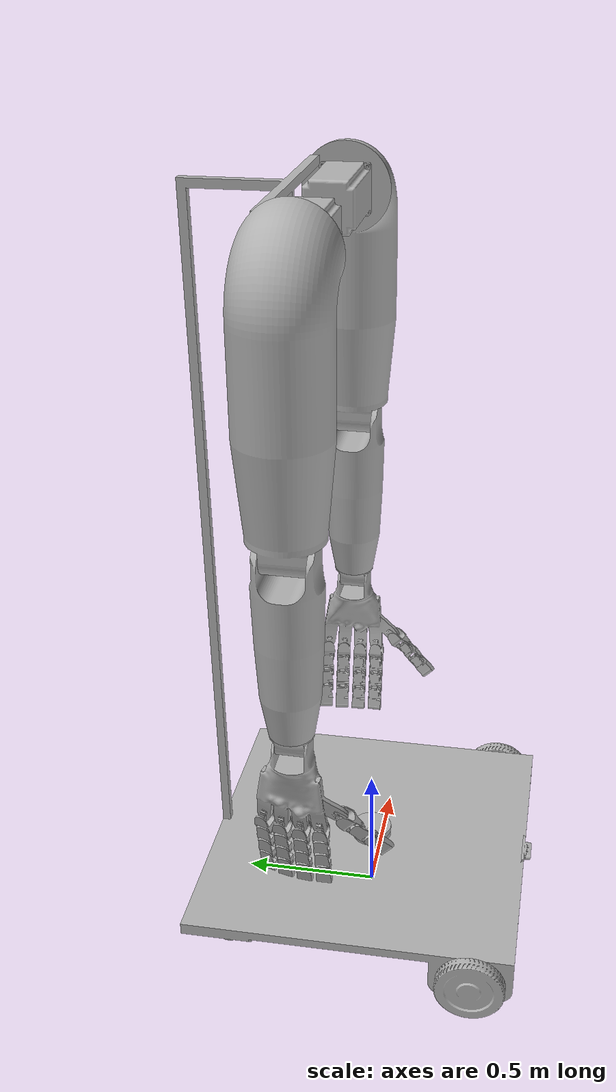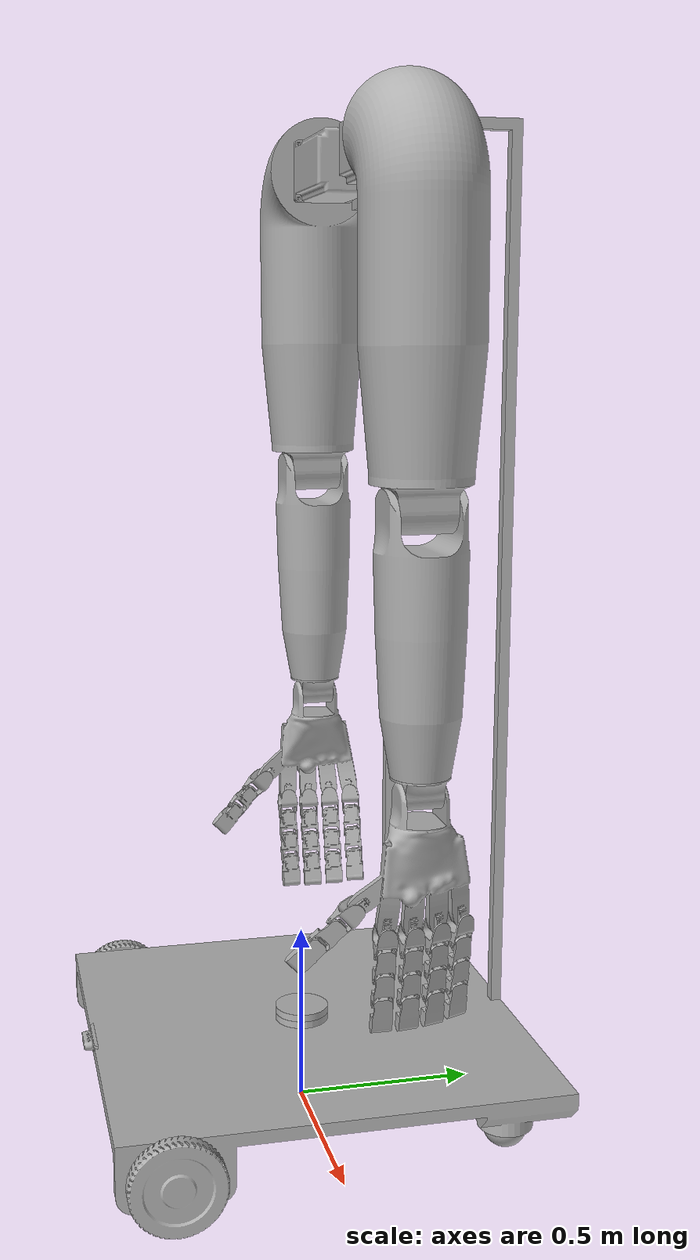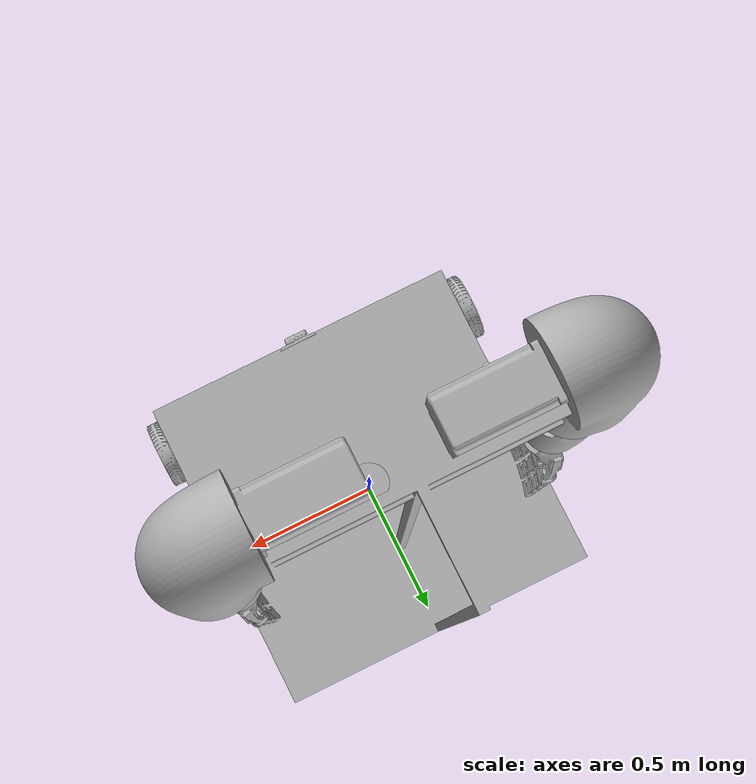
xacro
<?xml version="1.0" ?>
<robot name="hproject" xmlns:xacro="http://www.ros.org/wiki/xacro">

<xacro:include filename="$(find hproject_description)/urdf/materials.xacro" />
<xacro:include filename="$(find hproject_description)/urdf/hproject.trans" />
<xacro:include filename="$(find hproject_description)/urdf/hproject.gazebo" />
<link name="base_link">
  <inertial>
    <origin xyz="-3.1442865304222692e-15 0.26145061991792107 0.40081245927985315" rpy="0 0 0"/>
    <mass value="372.0085391721659"/>
    <inertia ixx="185.554019" iyy="184.647479" izz="91.735258" ixy="-0.0" iyz="-7.399111" ixz="-0.0"/>
  </inertial>
  <visual>
    <origin xyz="0 0 0" rpy="0 0 0"/>
    <geometry>
      <mesh filename="package://hproject_description/meshes/base_link.stl" scale="0.001 0.001 0.001"/>
    </geometry>
    <material name="silver"/>
  </visual>
  <collision>
    <origin xyz="0 0 0" rpy="0 0 0"/>
    <geometry>
      <mesh filename="package://hproject_description/meshes/base_link.stl" scale="0.001 0.001 0.001"/>
    </geometry>
  </collision>
</link>

<link name="pinky_lateral_link_R_1">
  <inertial>
    <origin xyz="0.025162658632176704 -0.006289922186428376 -0.018941953802106837" rpy="0 0 0"/>
    <mass value="0.3479532548461513"/>
    <inertia ixx="0.000218" iyy="0.000264" izz="0.000228" ixy="1.6e-05" iyz="3e-06" ixz="-1.3e-05"/>
  </inertial>
  <visual>
    <origin xyz="0.562592 -0.287941 -0.730502" rpy="0 0 0"/>
    <geometry>
      <mesh filename="package://hproject_description/meshes/pinky_lateral_link_R_1.stl" scale="0.001 0.001 0.001"/>
    </geometry>
    <material name="silver"/>
  </visual>
  <collision>
    <origin xyz="0.562592 -0.287941 -0.730502" rpy="0 0 0"/>
    <geometry>
      <mesh filename="package://hproject_description/meshes/pinky_lateral_link_R_1.stl" scale="0.001 0.001 0.001"/>
    </geometry>
  </collision>
</link>

<link name="pinky_proximal_link_R_1">
  <inertial>
    <origin xyz="0.00814301783439042 0.02563595324629586 -0.01601587517939662" rpy="0 0 0"/>
    <mass value="0.5045183303050147"/>
    <inertia ixx="0.000281" iyy="0.000232" izz="0.000139" ixy="-2e-05" iyz="-1.1e-05" ixz="3.5e-05"/>
  </inertial>
  <visual>
    <origin xyz="0.539271 -0.261682 -0.667654" rpy="0 0 0"/>
    <geometry>
      <mesh filename="package://hproject_description/meshes/pinky_proximal_link_R_1.stl" scale="0.001 0.001 0.001"/>
    </geometry>
    <material name="silver"/>
  </visual>
  <collision>
    <origin xyz="0.539271 -0.261682 -0.667654" rpy="0 0 0"/>
    <geometry>
      <mesh filename="package://hproject_description/meshes/pinky_proximal_link_R_1.stl" scale="0.001 0.001 0.001"/>
    </geometry>
  </collision>
</link>

<link name="pinky_middle_link_R_1">
  <inertial>
    <origin xyz="0.008142492931098144 0.02563617924072581 -0.016015666759633285" rpy="0 0 0"/>
    <mass value="0.5045183303050147"/>
    <inertia ixx="0.000281" iyy="0.000232" izz="0.000139" ixy="-2e-05" iyz="-1.1e-05" ixz="3.5e-05"/>
  </inertial>
  <visual>
    <origin xyz="0.523561 -0.262285 -0.599442" rpy="0 0 0"/>
    <geometry>
      <mesh filename="package://hproject_description/meshes/pinky_middle_link_R_1.stl" scale="0.001 0.001 0.001"/>
    </geometry>
    <material name="silver"/>
  </visual>
  <collision>
    <origin xyz="0.523561 -0.262285 -0.599442" rpy="0 0 0"/>
    <geometry>
      <mesh filename="package://hproject_description/meshes/pinky_middle_link_R_1.stl" scale="0.001 0.001 0.001"/>
    </geometry>
  </collision>
</link>

<link name="pinky_distal_link_R_1">
  <inertial>
    <origin xyz="0.012177417001750068 0.02489319154109454 -0.0341376857896431" rpy="0 0 0"/>
    <mass value="0.8633298630864712"/>
    <inertia ixx="0.000785" iyy="0.000716" izz="0.000247" ixy="-3e-05" iyz="-3.1e-05" ixz="0.000128"/>
  </inertial>
  <visual>
    <origin xyz="0.507852 -0.262888 -0.531231" rpy="0 0 0"/>
    <geometry>
      <mesh filename="package://hproject_description/meshes/pinky_distal_link_R_1.stl" scale="0.001 0.001 0.001"/>
    </geometry>
    <material name="silver"/>
  </visual>
  <collision>
    <origin xyz="0.507852 -0.262888 -0.531231" rpy="0 0 0"/>
    <geometry>
      <mesh filename="package://hproject_description/meshes/pinky_distal_link_R_1.stl" scale="0.001 0.001 0.001"/>
    </geometry>
  </collision>
</link>

<link name="link_pinky_lateral_L_1">
  <inertial>
    <origin xyz="-0.024527691415912933 -0.006161075301069352 -0.01979834319498286" rpy="0 0 0"/>
    <mass value="0.3479517187894897"/>
    <inertia ixx="0.000217" iyy="0.000264" izz="0.000229" ixy="-1.6e-05" iyz="3e-06" ixz="1.3e-05"/>
  </inertial>
  <visual>
    <origin xyz="-0.586789 -0.284862 -0.73061" rpy="0 0 0"/>
    <geometry>
      <mesh filename="package://hproject_description/meshes/link_pinky_lateral_L_1.stl" scale="0.001 0.001 0.001"/>
    </geometry>
    <material name="silver"/>
  </visual>
  <collision>
    <origin xyz="-0.586789 -0.284862 -0.73061" rpy="0 0 0"/>
    <geometry>
      <mesh filename="package://hproject_description/meshes/link_pinky_lateral_L_1.stl" scale="0.001 0.001 0.001"/>
    </geometry>
  </collision>
</link>

<link name="pinky_proximal_link_L_1">
  <inertial>
    <origin xyz="-0.007413918376508732 0.02566000570705468 -0.016327788143534416" rpy="0 0 0"/>
    <mass value="0.5045183290191879"/>
    <inertia ixx="0.000283" iyy="0.000232" izz="0.000137" ixy="2e-05" iyz="-1e-05" ixz="-3e-05"/>
  </inertial>
  <visual>
    <origin xyz="-0.565502 -0.258646 -0.667026" rpy="0 0 0"/>
    <geometry>
      <mesh filename="package://hproject_description/meshes/pinky_proximal_link_L_1.stl" scale="0.001 0.001 0.001"/>
    </geometry>
    <material name="silver"/>
  </visual>
  <collision>
    <origin xyz="-0.565502 -0.258646 -0.667026" rpy="0 0 0"/>
    <geometry>
      <mesh filename="package://hproject_description/meshes/pinky_proximal_link_L_1.stl" scale="0.001 0.001 0.001"/>
    </geometry>
  </collision>
</link>

<link name="pinky_middle_link_L_1">
  <inertial>
    <origin xyz="-0.007414179541616939 0.025660688378556284 -0.016328431255089537" rpy="0 0 0"/>
    <mass value="0.5045183290191879"/>
    <inertia ixx="0.000283" iyy="0.000232" izz="0.000137" ixy="2e-05" iyz="-1e-05" ixz="-3e-05"/>
  </inertial>
  <visual>
    <origin xyz="-0.552183 -0.259233 -0.598308" rpy="0 0 0"/>
    <geometry>
      <mesh filename="package://hproject_description/meshes/pinky_middle_link_L_1.stl" scale="0.001 0.001 0.001"/>
    </geometry>
    <material name="silver"/>
  </visual>
  <collision>
    <origin xyz="-0.552183 -0.259233 -0.598308" rpy="0 0 0"/>
    <geometry>
      <mesh filename="package://hproject_description/meshes/pinky_middle_link_L_1.stl" scale="0.001 0.001 0.001"/>
    </geometry>
  </collision>
</link>

<link name="pinky_distal_link_L_1">
  <inertial>
    <origin xyz="-0.01081982406193649 0.024912158357957292 -0.0345777749693556" rpy="0 0 0"/>
    <mass value="0.8633298618006443"/>
    <inertia ixx="0.000793" iyy="0.000715" izz="0.000239" ixy="3e-05" iyz="-3e-05" ixz="-0.000109"/>
  </inertial>
  <visual>
    <origin xyz="-0.538864 -0.259821 -0.529589" rpy="0 0 0"/>
    <geometry>
      <mesh filename="package://hproject_description/meshes/pinky_distal_link_L_1.stl" scale="0.001 0.001 0.001"/>
    </geometry>
    <material name="silver"/>
  </visual>
  <collision>
    <origin xyz="-0.538864 -0.259821 -0.529589" rpy="0 0 0"/>
    <geometry>
      <mesh filename="package://hproject_description/meshes/pinky_distal_link_L_1.stl" scale="0.001 0.001 0.001"/>
    </geometry>
  </collision>
</link>

<link name="ring_lateral_link_R_1">
  <inertial>
    <origin xyz="0.02571055170450487 -0.004236376693551258 -0.018774979296162453" rpy="0 0 0"/>
    <mass value="0.3479532548461513"/>
    <inertia ixx="0.000216" iyy="0.000266" izz="0.000228" ixy="1.1e-05" iyz="1e-06" ixz="-1.4e-05"/>
  </inertial>
  <visual>
    <origin xyz="0.57759 -0.221317 -0.720877" rpy="0 0 0"/>
    <geometry>
      <mesh filename="package://hproject_description/meshes/ring_lateral_link_R_1.stl" scale="0.001 0.001 0.001"/>
    </geometry>
    <material name="silver"/>
  </visual>
  <collision>
    <origin xyz="0.57759 -0.221317 -0.720877" rpy="0 0 0"/>
    <geometry>
      <mesh filename="package://hproject_description/meshes/ring_lateral_link_R_1.stl" scale="0.001 0.001 0.001"/>
    </geometry>
  </collision>
</link>

<link name="ring_proximal_link_R_1">
  <inertial>
    <origin xyz="0.005661892633136656 0.025941892956582002 -0.016583245911054423" rpy="0 0 0"/>
    <mass value="0.5045183303050147"/>
    <inertia ixx="0.000284" iyy="0.000228" izz="0.000139" ixy="-1.4e-05" iyz="-9e-06" ixz="3.7e-05"/>
  </inertial>
  <visual>
    <origin xyz="0.551641 -0.196051 -0.658656" rpy="0 0 0"/>
    <geometry>
      <mesh filename="package://hproject_description/meshes/ring_proximal_link_R_1.stl" scale="0.001 0.001 0.001"/>
    </geometry>
    <material name="silver"/>
  </visual>
  <collision>
    <origin xyz="0.551641 -0.196051 -0.658656" rpy="0 0 0"/>
    <geometry>
      <mesh filename="package://hproject_description/meshes/ring_proximal_link_R_1.stl" scale="0.001 0.001 0.001"/>
    </geometry>
  </collision>
</link>

<link name="ring_middle_link_R_1">
  <inertial>
    <origin xyz="0.005662442671585888 0.02594174456919049 -0.016582632928191843" rpy="0 0 0"/>
    <mass value="0.5045183303050147"/>
    <inertia ixx="0.000284" iyy="0.000228" izz="0.000139" ixy="-1.4e-05" iyz="-9e-06" ixz="3.7e-05"/>
  </inertial>
  <visual>
    <origin xyz="0.535861 -0.196654 -0.59046" rpy="0 0 0"/>
    <geometry>
      <mesh filename="package://hproject_description/meshes/ring_middle_link_R_1.stl" scale="0.001 0.001 0.001"/>
    </geometry>
    <material name="silver"/>
  </visual>
  <collision>
    <origin xyz="0.535861 -0.196654 -0.59046" rpy="0 0 0"/>
    <geometry>
      <mesh filename="package://hproject_description/meshes/ring_middle_link_R_1.stl" scale="0.001 0.001 0.001"/>
    </geometry>
  </collision>
</link>

<link name="ring_distal_link_R_1">
  <inertial>
    <origin xyz="0.009803733546907223 0.025189283216207614 -0.03467965050040267" rpy="0 0 0"/>
    <mass value="0.8633298630864712"/>
    <inertia ixx="0.000789" iyy="0.00071" izz="0.000249" ixy="-2e-05" iyz="-2.9e-05" ixz="0.000133"/>
  </inertial>
  <visual>
    <origin xyz="0.52008 -0.197257 -0.522265" rpy="0 0 0"/>
    <geometry>
      <mesh filename="package://hproject_description/meshes/ring_distal_link_R_1.stl" scale="0.001 0.001 0.001"/>
    </geometry>
    <material name="silver"/>
  </visual>
  <collision>
    <origin xyz="0.52008 -0.197257 -0.522265" rpy="0 0 0"/>
    <geometry>
      <mesh filename="package://hproject_description/meshes/ring_distal_link_R_1.stl" scale="0.001 0.001 0.001"/>
    </geometry>
  </collision>
</link>

<link name="link_ring_lateral_L_1">
  <inertial>
    <origin xyz="-0.025068117243347232 -0.00410372994431632 -0.01965359769458941" rpy="0 0 0"/>
    <mass value="0.3479517187894897"/>
    <inertia ixx="0.000215" iyy="0.000266" izz="0.000229" ixy="-1.1e-05" iyz="1e-06" ixz="1.3e-05"/>
  </inertial>
  <visual>
    <origin xyz="-0.601683 -0.218127 -0.721612" rpy="0 0 0"/>
    <geometry>
      <mesh filename="package://hproject_description/meshes/link_ring_lateral_L_1.stl" scale="0.001 0.001 0.001"/>
    </geometry>
    <material name="silver"/>
  </visual>
  <collision>
    <origin xyz="-0.601683 -0.218127 -0.721612" rpy="0 0 0"/>
    <geometry>
      <mesh filename="package://hproject_description/meshes/link_ring_lateral_L_1.stl" scale="0.001 0.001 0.001"/>
    </geometry>
  </collision>
</link>

<link name="ring_proximal_link_L_1">
  <inertial>
    <origin xyz="-0.004913712354940314 0.02594901740828881 -0.01680823152975408" rpy="0 0 0"/>
    <mass value="0.5045183290191879"/>
    <inertia ixx="0.000286" iyy="0.000228" izz="0.000137" ixy="1.4e-05" iyz="-9e-06" ixz="-3.2e-05"/>
  </inertial>
  <visual>
    <origin xyz="-0.577755 -0.192922 -0.658561" rpy="0 0 0"/>
    <geometry>
      <mesh filename="package://hproject_description/meshes/ring_proximal_link_L_1.stl" scale="0.001 0.001 0.001"/>
    </geometry>
    <material name="silver"/>
  </visual>
  <collision>
    <origin xyz="-0.577755 -0.192922 -0.658561" rpy="0 0 0"/>
    <geometry>
      <mesh filename="package://hproject_description/meshes/ring_proximal_link_L_1.stl" scale="0.001 0.001 0.001"/>
    </geometry>
  </collision>
</link>

<link name="ring_middle_link_L_1">
  <inertial>
    <origin xyz="-0.004913577772976074 0.025948808665132606 -0.016808956438558176" rpy="0 0 0"/>
    <mass value="0.5045183290191879"/>
    <inertia ixx="0.000286" iyy="0.000228" izz="0.000137" ixy="1.4e-05" iyz="-9e-06" ixz="-3.2e-05"/>
  </inertial>
  <visual>
    <origin xyz="-0.564364 -0.19351 -0.589857" rpy="0 0 0"/>
    <geometry>
      <mesh filename="package://hproject_description/meshes/ring_middle_link_L_1.stl" scale="0.001 0.001 0.001"/>
    </geometry>
    <material name="silver"/>
  </visual>
  <collision>
    <origin xyz="-0.564364 -0.19351 -0.589857" rpy="0 0 0"/>
    <geometry>
      <mesh filename="package://hproject_description/meshes/ring_middle_link_L_1.stl" scale="0.001 0.001 0.001"/>
    </geometry>
  </collision>
</link>

<link name="ring_distal_link_L_1">
  <inertial>
    <origin xyz="-0.008426966734240815 0.025193016930298795 -0.035037525649868895" rpy="0 0 0"/>
    <mass value="0.8633298618006443"/>
    <inertia ixx="0.000798" iyy="0.000709" izz="0.00024" ixy="2e-05" iyz="-2.8e-05" ixz="-0.000114"/>
  </inertial>
  <visual>
    <origin xyz="-0.550973 -0.194097 -0.521152" rpy="0 0 0"/>
    <geometry>
      <mesh filename="package://hproject_description/meshes/ring_distal_link_L_1.stl" scale="0.001 0.001 0.001"/>
    </geometry>
    <material name="silver"/>
  </visual>
  <collision>
    <origin xyz="-0.550973 -0.194097 -0.521152" rpy="0 0 0"/>
    <geometry>
      <mesh filename="package://hproject_description/meshes/ring_distal_link_L_1.stl" scale="0.001 0.001 0.001"/>
    </geometry>
  </collision>
</link>

<link name="middle_lateral_link_R_1">
  <inertial>
    <origin xyz="0.026041180796861907 -0.0020864946234349646 -0.018682630597832373" rpy="0 0 0"/>
    <mass value="0.3479532548461513"/>
    <inertia ixx="0.000214" iyy="0.000268" izz="0.000228" ixy="5e-06" iyz="-1e-06" ixz="-1.4e-05"/>
  </inertial>
  <visual>
    <origin xyz="0.586212 -0.151415 -0.717139" rpy="0 0 0"/>
    <geometry>
      <mesh filename="package://hproject_description/meshes/middle_lateral_link_R_1.stl" scale="0.001 0.001 0.001"/>
    </geometry>
    <material name="silver"/>
  </visual>
  <collision>
    <origin xyz="0.586212 -0.151415 -0.717139" rpy="0 0 0"/>
    <geometry>
      <mesh filename="package://hproject_description/meshes/middle_lateral_link_R_1.stl" scale="0.001 0.001 0.001"/>
    </geometry>
  </collision>
</link>

<link name="middle_proximal_link_R_1">
  <inertial>
    <origin xyz="0.003084007897529828 0.02598848910702689 -0.01717941289796998" rpy="0 0 0"/>
    <mass value="0.5045183303050147"/>
    <inertia ixx="0.000286" iyy="0.000226" izz="0.00014" ixy="-8e-06" iyz="-8e-06" ixz="3.8e-05"/>
  </inertial>
  <visual>
    <origin xyz="0.557757 -0.127434 -0.655507" rpy="0 0 0"/>
    <geometry>
      <mesh filename="package://hproject_description/meshes/middle_proximal_link_R_1.stl" scale="0.001 0.001 0.001"/>
    </geometry>
    <material name="silver"/>
  </visual>
  <collision>
    <origin xyz="0.557757 -0.127434 -0.655507" rpy="0 0 0"/>
    <geometry>
      <mesh filename="package://hproject_description/meshes/middle_proximal_link_R_1.stl" scale="0.001 0.001 0.001"/>
    </geometry>
  </collision>
</link>

<link name="middle_middle_link_R_1">
  <inertial>
    <origin xyz="0.0030845979737750273 0.02598837741360413 -0.017179409765841536" rpy="0 0 0"/>
    <mass value="0.5045183303050147"/>
    <inertia ixx="0.000286" iyy="0.000226" izz="0.00014" ixy="-8e-06" iyz="-8e-06" ixz="3.8e-05"/>
  </inertial>
  <visual>
    <origin xyz="0.541984 -0.128037 -0.58731" rpy="0 0 0"/>
    <geometry>
      <mesh filename="package://hproject_description/meshes/middle_middle_link_R_1.stl" scale="0.001 0.001 0.001"/>
    </geometry>
    <material name="silver"/>
  </visual>
  <collision>
    <origin xyz="0.541984 -0.128037 -0.58731" rpy="0 0 0"/>
    <geometry>
      <mesh filename="package://hproject_description/meshes/middle_middle_link_R_1.stl" scale="0.001 0.001 0.001"/>
    </geometry>
  </collision>
</link>

<link name="middle_distal_link_R_1">
  <inertial>
    <origin xyz="0.00731510402745339 0.025236171160077647 -0.03525540544897515" rpy="0 0 0"/>
    <mass value="0.8633298630864712"/>
    <inertia ixx="0.000792" iyy="0.000706" izz="0.00025" ixy="-8e-06" iyz="-2.6e-05" ixz="0.000136"/>
  </inertial>
  <visual>
    <origin xyz="0.52621 -0.12864 -0.519113" rpy="0 0 0"/>
    <geometry>
      <mesh filename="package://hproject_description/meshes/middle_distal_link_R_1.stl" scale="0.001 0.001 0.001"/>
    </geometry>
    <material name="silver"/>
  </visual>
  <collision>
    <origin xyz="0.52621 -0.12864 -0.519113" rpy="0 0 0"/>
    <geometry>
      <mesh filename="package://hproject_description/meshes/middle_distal_link_R_1.stl" scale="0.001 0.001 0.001"/>
    </geometry>
  </collision>
</link>

<link name="middle_lateral_link_L_1">
  <inertial>
    <origin xyz="-0.025387457639369115 -0.001951655562393212 -0.01957494155610262" rpy="0 0 0"/>
    <mass value="0.3479517187894897"/>
    <inertia ixx="0.000213" iyy="0.000268" izz="0.000229" ixy="-5e-06" iyz="-1e-06" ixz="1.4e-05"/>
  </inertial>
  <visual>
    <origin xyz="-0.609978 -0.148165 -0.718279" rpy="0 0 0"/>
    <geometry>
      <mesh filename="package://hproject_description/meshes/middle_lateral_link_L_1.stl" scale="0.001 0.001 0.001"/>
    </geometry>
    <material name="silver"/>
  </visual>
  <collision>
    <origin xyz="-0.609978 -0.148165 -0.718279" rpy="0 0 0"/>
    <geometry>
      <mesh filename="package://hproject_description/meshes/middle_lateral_link_L_1.stl" scale="0.001 0.001 0.001"/>
    </geometry>
  </collision>
</link>

<link name="middle_proximal_link_L_1">
  <inertial>
    <origin xyz="-0.002315609723158696 0.0259780834137361 -0.017314793423498398" rpy="0 0 0"/>
    <mass value="0.5045183290191879"/>
    <inertia ixx="0.000289" iyy="0.000226" izz="0.000137" ixy="8e-06" iyz="-7e-06" ixz="-3.3e-05"/>
  </inertial>
  <visual>
    <origin xyz="-0.583533 -0.124262 -0.655729" rpy="0 0 0"/>
    <geometry>
      <mesh filename="package://hproject_description/meshes/middle_proximal_link_L_1.stl" scale="0.001 0.001 0.001"/>
    </geometry>
    <material name="silver"/>
  </visual>
  <collision>
    <origin xyz="-0.583533 -0.124262 -0.655729" rpy="0 0 0"/>
    <geometry>
      <mesh filename="package://hproject_description/meshes/middle_proximal_link_L_1.stl" scale="0.001 0.001 0.001"/>
    </geometry>
  </collision>
</link>

<link name="middle_middle_link_L_1">
  <inertial>
    <origin xyz="-0.0023154632263140407 0.02597886406447615 -0.0173138847059513" rpy="0 0 0"/>
    <mass value="0.5045183290191879"/>
    <inertia ixx="0.000289" iyy="0.000226" izz="0.000137" ixy="8e-06" iyz="-7e-06" ixz="-3.3e-05"/>
  </inertial>
  <visual>
    <origin xyz="-0.570149 -0.124849 -0.587022" rpy="0 0 0"/>
    <geometry>
      <mesh filename="package://hproject_description/meshes/middle_middle_link_L_1.stl" scale="0.001 0.001 0.001"/>
    </geometry>
    <material name="silver"/>
  </visual>
  <collision>
    <origin xyz="-0.570149 -0.124849 -0.587022" rpy="0 0 0"/>
    <geometry>
      <mesh filename="package://hproject_description/meshes/middle_middle_link_L_1.stl" scale="0.001 0.001 0.001"/>
    </geometry>
  </collision>
</link>

<link name="middle_distal_link_L_1">
  <inertial>
    <origin xyz="-0.005919676800920204 0.025222886160198882 -0.035525309144413264" rpy="0 0 0"/>
    <mass value="0.8633298618006443"/>
    <inertia ixx="0.000801" iyy="0.000705" izz="0.000241" ixy="8e-06" iyz="-2.6e-05" ixz="-0.000117"/>
  </inertial>
  <visual>
    <origin xyz="-0.556766 -0.125437 -0.518316" rpy="0 0 0"/>
    <geometry>
      <mesh filename="package://hproject_description/meshes/middle_distal_link_L_1.stl" scale="0.001 0.001 0.001"/>
    </geometry>
    <material name="silver"/>
  </visual>
  <collision>
    <origin xyz="-0.556766 -0.125437 -0.518316" rpy="0 0 0"/>
    <geometry>
      <mesh filename="package://hproject_description/meshes/middle_distal_link_L_1.stl" scale="0.001 0.001 0.001"/>
    </geometry>
  </collision>
</link>

<link name="index_lateral_link_R_1">
  <inertial>
    <origin xyz="0.026129259283667827 9.996581454410625e-05 -0.018674589799297925" rpy="0 0 0"/>
    <mass value="0.3479532548461513"/>
    <inertia ixx="0.000214" iyy="0.000268" izz="0.000228" ixy="-0.0" iyz="-3e-06" ixz="-1.4e-05"/>
  </inertial>
  <visual>
    <origin xyz="0.58867 -0.080955 -0.719254" rpy="0 0 0"/>
    <geometry>
      <mesh filename="package://hproject_description/meshes/index_lateral_link_R_1.stl" scale="0.001 0.001 0.001"/>
    </geometry>
    <material name="silver"/>
  </visual>
  <collision>
    <origin xyz="0.58867 -0.080955 -0.719254" rpy="0 0 0"/>
    <geometry>
      <mesh filename="package://hproject_description/meshes/index_lateral_link_R_1.stl" scale="0.001 0.001 0.001"/>
    </geometry>
  </collision>
</link>

<link name="index_proximal_link_R_1">
  <inertial>
    <origin xyz="0.0004757516462724487 0.025762531083408265 -0.017778345421928132" rpy="0 0 0"/>
    <mass value="0.5045183303050147"/>
    <inertia ixx="0.000287" iyy="0.000224" izz="0.00014" ixy="-1e-06" iyz="-6e-06" ixz="3.9e-05"/>
  </inertial>
  <visual>
    <origin xyz="0.557923 -0.058526 -0.658141" rpy="0 0 0"/>
    <geometry>
      <mesh filename="package://hproject_description/meshes/index_proximal_link_R_1.stl" scale="0.001 0.001 0.001"/>
    </geometry>
    <material name="silver"/>
  </visual>
  <collision>
    <origin xyz="0.557923 -0.058526 -0.658141" rpy="0 0 0"/>
    <geometry>
      <mesh filename="package://hproject_description/meshes/index_proximal_link_R_1.stl" scale="0.001 0.001 0.001"/>
    </geometry>
  </collision>
</link>

<link name="index_middle_link_R_1">
  <inertial>
    <origin xyz="0.0004754197008374206 0.025762955920113947 -0.01777883133967917" rpy="0 0 0"/>
    <mass value="0.5045183303050147"/>
    <inertia ixx="0.000287" iyy="0.000224" izz="0.00014" ixy="-1e-06" iyz="-6e-06" ixz="3.9e-05"/>
  </inertial>
  <visual>
    <origin xyz="0.542251 -0.059129 -0.589921" rpy="0 0 0"/>
    <geometry>
      <mesh filename="package://hproject_description/meshes/index_middle_link_R_1.stl" scale="0.001 0.001 0.001"/>
    </geometry>
    <material name="silver"/>
  </visual>
  <collision>
    <origin xyz="0.542251 -0.059129 -0.589921" rpy="0 0 0"/>
    <geometry>
      <mesh filename="package://hproject_description/meshes/index_middle_link_R_1.stl" scale="0.001 0.001 0.001"/>
    </geometry>
  </collision>
</link>

<link name="index_distal_link_R_1">
  <inertial>
    <origin xyz="0.004771055369809374 0.02502026571335996 -0.0358396169852539" rpy="0 0 0"/>
    <mass value="0.8633298630864712"/>
    <inertia ixx="0.000792" iyy="0.000704" izz="0.000251" ixy="4e-06" iyz="-2.3e-05" ixz="0.000138"/>
  </inertial>
  <visual>
    <origin xyz="0.52658 -0.059733 -0.5217" rpy="0 0 0"/>
    <geometry>
      <mesh filename="package://hproject_description/meshes/index_distal_link_R_1.stl" scale="0.001 0.001 0.001"/>
    </geometry>
    <material name="silver"/>
  </visual>
  <collision>
    <origin xyz="0.52658 -0.059733 -0.5217" rpy="0 0 0"/>
    <geometry>
      <mesh filename="package://hproject_description/meshes/index_distal_link_R_1.stl" scale="0.001 0.001 0.001"/>
    </geometry>
  </collision>
</link>

<link name="index_lateral_link_L_1">
  <inertial>
    <origin xyz="-0.025461874332055157 0.0002357379172765739 -0.019574692794462" rpy="0 0 0"/>
    <mass value="0.3479517187894897"/>
    <inertia ixx="0.000213" iyy="0.000268" izz="0.000229" ixy="1e-06" iyz="-3e-06" ixz="1.3e-05"/>
  </inertial>
  <visual>
    <origin xyz="-0.611906 -0.077694 -0.720584" rpy="0 0 0"/>
    <geometry>
      <mesh filename="package://hproject_description/meshes/index_lateral_link_L_1.stl" scale="0.001 0.001 0.001"/>
    </geometry>
    <material name="silver"/>
  </visual>
  <collision>
    <origin xyz="-0.611906 -0.077694 -0.720584" rpy="0 0 0"/>
    <geometry>
      <mesh filename="package://hproject_description/meshes/index_lateral_link_L_1.stl" scale="0.001 0.001 0.001"/>
    </geometry>
  </collision>
</link>

<link name="index_proximal_link_L_1">
  <inertial>
    <origin xyz="0.0003105627917185938 0.025735344989623286 -0.017822101827893233" rpy="0 0 0"/>
    <mass value="0.5045183290191879"/>
    <inertia ixx="0.000289" iyy="0.000224" izz="0.000138" ixy="0.0" iyz="-6e-06" ixz="-3.4e-05"/>
  </inertial>
  <visual>
    <origin xyz="-0.583162 -0.055358 -0.658469" rpy="0 0 0"/>
    <geometry>
      <mesh filename="package://hproject_description/meshes/index_proximal_link_L_1.stl" scale="0.001 0.001 0.001"/>
    </geometry>
    <material name="silver"/>
  </visual>
  <collision>
    <origin xyz="-0.583162 -0.055358 -0.658469" rpy="0 0 0"/>
    <geometry>
      <mesh filename="package://hproject_description/meshes/index_proximal_link_L_1.stl" scale="0.001 0.001 0.001"/>
    </geometry>
  </collision>
</link>

<link name="index_middle_link_L_1">
  <inertial>
    <origin xyz="0.0003103891173434903 0.025734969651762925 -0.017822116721000314" rpy="0 0 0"/>
    <mass value="0.5045183290191879"/>
    <inertia ixx="0.000289" iyy="0.000224" izz="0.000138" ixy="0.0" iyz="-6e-06" ixz="-3.4e-05"/>
  </inertial>
  <visual>
    <origin xyz="-0.569881 -0.055946 -0.589743" rpy="0 0 0"/>
    <geometry>
      <mesh filename="package://hproject_description/meshes/index_middle_link_L_1.stl" scale="0.001 0.001 0.001"/>
    </geometry>
    <material name="silver"/>
  </visual>
  <collision>
    <origin xyz="-0.569881 -0.055946 -0.589743" rpy="0 0 0"/>
    <geometry>
      <mesh filename="package://hproject_description/meshes/index_middle_link_L_1.stl" scale="0.001 0.001 0.001"/>
    </geometry>
  </collision>
</link>

<link name="index_distal_link_L_1">
  <inertial>
    <origin xyz="-0.0033576037056979313 0.02498925014840396 -0.03602102154961734" rpy="0 0 0"/>
    <mass value="0.8633298618006443"/>
    <inertia ixx="0.000801" iyy="0.000704" izz="0.000242" ixy="-4e-06" iyz="-2.3e-05" ixz="-0.000119"/>
  </inertial>
  <visual>
    <origin xyz="-0.5566 -0.056534 -0.521017" rpy="0 0 0"/>
    <geometry>
      <mesh filename="package://hproject_description/meshes/index_distal_link_L_1.stl" scale="0.001 0.001 0.001"/>
    </geometry>
    <material name="silver"/>
  </visual>
  <collision>
    <origin xyz="-0.5566 -0.056534 -0.521017" rpy="0 0 0"/>
    <geometry>
      <mesh filename="package://hproject_description/meshes/index_distal_link_L_1.stl" scale="0.001 0.001 0.001"/>
    </geometry>
  </collision>
</link>

<link name="thumb_lateral_link_R_1">
  <inertial>
    <origin xyz="0.02571732411381944 -0.013214280584982882 -0.01398286188078901" rpy="0 0 0"/>
    <mass value="0.3479532548461513"/>
    <inertia ixx="0.000213" iyy="0.000244" izz="0.000252" ixy="-1.1e-05" iyz="-2e-05" ixz="-8e-06"/>
  </inertial>
  <visual>
    <origin xyz="0.590827 -0.002272 -0.787828" rpy="0 0 0"/>
    <geometry>
      <mesh filename="package://hproject_description/meshes/thumb_lateral_link_R_1.stl" scale="0.001 0.001 0.001"/>
    </geometry>
    <material name="silver"/>
  </visual>
  <collision>
    <origin xyz="0.590827 -0.002272 -0.787828" rpy="0 0 0"/>
    <geometry>
      <mesh filename="package://hproject_description/meshes/thumb_lateral_link_R_1.stl" scale="0.001 0.001 0.001"/>
    </geometry>
  </collision>
</link>

<link name="thumb_proximal_link_R_1">
  <inertial>
    <origin xyz="-0.0005535667325509142 0.005302347341027434 -0.030848360827002264" rpy="0 0 0"/>
    <mass value="0.5045183303050147"/>
    <inertia ixx="0.000288" iyy="0.000176" izz="0.000187" ixy="2.6e-05" iyz="-4.3e-05" ixz="2.4e-05"/>
  </inertial>
  <visual>
    <origin xyz="0.560822 0.057023 -0.760133" rpy="0 0 0"/>
    <geometry>
      <mesh filename="package://hproject_description/meshes/thumb_proximal_link_R_1.stl" scale="0.001 0.001 0.001"/>
    </geometry>
    <material name="silver"/>
  </visual>
  <collision>
    <origin xyz="0.560822 0.057023 -0.760133" rpy="0 0 0"/>
    <geometry>
      <mesh filename="package://hproject_description/meshes/thumb_proximal_link_R_1.stl" scale="0.001 0.001 0.001"/>
    </geometry>
  </collision>
</link>

<link name="thumb_distal_link_R_1">
  <inertial>
    <origin xyz="0.0033753339775390856 -0.008117596515754014 -0.04308153441451379" rpy="0 0 0"/>
    <mass value="0.8633298630864712"/>
    <inertia ixx="0.000798" iyy="0.00045" izz="0.000499" ixy="9.5e-05" iyz="-0.000229" ixz="8.5e-05"/>
  </inertial>
  <visual>
    <origin xyz="0.546618 0.105336 -0.71151" rpy="0 0 0"/>
    <geometry>
      <mesh filename="package://hproject_description/meshes/thumb_distal_link_R_1.stl" scale="0.001 0.001 0.001"/>
    </geometry>
    <material name="silver"/>
  </visual>
  <collision>
    <origin xyz="0.546618 0.105336 -0.71151" rpy="0 0 0"/>
    <geometry>
      <mesh filename="package://hproject_description/meshes/thumb_distal_link_R_1.stl" scale="0.001 0.001 0.001"/>
    </geometry>
  </collision>
</link>

<link name="thumb_lateral_link_L_1">
  <inertial>
    <origin xyz="-0.025299166039594367 -0.013073222489963295 -0.014851050454191328" rpy="0 0 0"/>
    <mass value="0.3479517187894897"/>
    <inertia ixx="0.000213" iyy="0.000244" izz="0.000253" ixy="1.2e-05" iyz="-1.9e-05" ixz="7e-06"/>
  </inertial>
  <visual>
    <origin xyz="-0.611164 0.000884 -0.789307" rpy="0 0 0"/>
    <geometry>
      <mesh filename="package://hproject_description/meshes/thumb_lateral_link_L_1.stl" scale="0.001 0.001 0.001"/>
    </geometry>
    <material name="silver"/>
  </visual>
  <collision>
    <origin xyz="-0.611164 0.000884 -0.789307" rpy="0 0 0"/>
    <geometry>
      <mesh filename="package://hproject_description/meshes/thumb_lateral_link_L_1.stl" scale="0.001 0.001 0.001"/>
    </geometry>
  </collision>
</link>

<link name="thumb_proximal_link_L_1">
  <inertial>
    <origin xyz="0.0016631345011894894 0.005246352586244549 -0.030817304816391444" rpy="0 0 0"/>
    <mass value="0.5045183290191879"/>
    <inertia ixx="0.00029" iyy="0.000176" izz="0.000186" ixy="-2.5e-05" iyz="-4.4e-05" ixz="-2.1e-05"/>
  </inertial>
  <visual>
    <origin xyz="-0.581759 0.060033 -0.76067" rpy="0 0 0"/>
    <geometry>
      <mesh filename="package://hproject_description/meshes/thumb_proximal_link_L_1.stl" scale="0.001 0.001 0.001"/>
    </geometry>
    <material name="silver"/>
  </visual>
  <collision>
    <origin xyz="-0.581759 0.060033 -0.76067" rpy="0 0 0"/>
    <geometry>
      <mesh filename="package://hproject_description/meshes/thumb_proximal_link_L_1.stl" scale="0.001 0.001 0.001"/>
    </geometry>
  </collision>
</link>

<link name="thumb_distal_link_L_1">
  <inertial>
    <origin xyz="-0.0019248391013558797 -0.008169731269854028 -0.043161127717219694" rpy="0 0 0"/>
    <mass value="0.8633298618006443"/>
    <inertia ixx="0.000802" iyy="0.000451" izz="0.000494" ixy="-8.9e-05" iyz="-0.000232" ixz="-7.6e-05"/>
  </inertial>
  <visual>
    <origin xyz="-0.568947 0.108336 -0.711654" rpy="0 0 0"/>
    <geometry>
      <mesh filename="package://hproject_description/meshes/thumb_distal_link_L_1.stl" scale="0.001 0.001 0.001"/>
    </geometry>
    <material name="silver"/>
  </visual>
  <collision>
    <origin xyz="-0.568947 0.108336 -0.711654" rpy="0 0 0"/>
    <geometry>
      <mesh filename="package://hproject_description/meshes/thumb_distal_link_L_1.stl" scale="0.001 0.001 0.001"/>
    </geometry>
  </collision>
</link>

<link name="right_motor_link_1">
  <inertial>
    <origin xyz="-0.24689223684959732 -0.08499999999999938 -0.20000000000000062" rpy="0 0 0"/>
    <mass value="64.9703996435649"/>
    <inertia ixx="0.287636" iyy="0.64052" izz="0.64052" ixy="0.0" iyz="0.0" ixz="-0.0"/>
  </inertial>
  <visual>
    <origin xyz="0.015 -0.24 -2.825" rpy="0 0 0"/>
    <geometry>
      <mesh filename="package://hproject_description/meshes/right_motor_link_1.stl" scale="0.001 0.001 0.001"/>
    </geometry>
    <material name="silver"/>
  </visual>
  <collision>
    <origin xyz="0.015 -0.24 -2.825" rpy="0 0 0"/>
    <geometry>
      <mesh filename="package://hproject_description/meshes/right_motor_link_1.stl" scale="0.001 0.001 0.001"/>
    </geometry>
  </collision>
</link>

<link name="left_motor_link_1">
  <inertial>
    <origin xyz="0.2468922368495965 -0.08500000000000144 -0.20000000000000062" rpy="0 0 0"/>
    <mass value="64.9703996435649"/>
    <inertia ixx="0.287636" iyy="0.64052" izz="0.64052" ixy="0.0" iyz="0.0" ixz="0.0"/>
  </inertial>
  <visual>
    <origin xyz="-0.015 -0.24 -2.825" rpy="0 0 0"/>
    <geometry>
      <mesh filename="package://hproject_description/meshes/left_motor_link_1.stl" scale="0.001 0.001 0.001"/>
    </geometry>
    <material name="silver"/>
  </visual>
  <collision>
    <origin xyz="-0.015 -0.24 -2.825" rpy="0 0 0"/>
    <geometry>
      <mesh filename="package://hproject_description/meshes/left_motor_link_1.stl" scale="0.001 0.001 0.001"/>
    </geometry>
  </collision>
</link>

<link name="upper_arm_link_R_1">
  <inertial>
    <origin xyz="-0.14275700521289975 0.0033688042580595767 -0.3536701183723068" rpy="0 0 0"/>
    <mass value="487.64578453226363"/>
    <inertia ixx="36.376989" iyy="36.428356" izz="5.239192" ixy="0.014954" iyz="0.297112" ixz="-1.569957"/>
  </inertial>
  <visual>
    <origin xyz="0.414 -0.155 -2.625" rpy="0 0 0"/>
    <geometry>
      <mesh filename="package://hproject_description/meshes/upper_arm_link_R_1.stl" scale="0.001 0.001 0.001"/>
    </geometry>
    <material name="silver"/>
  </visual>
  <collision>
    <origin xyz="0.414 -0.155 -2.625" rpy="0 0 0"/>
    <geometry>
      <mesh filename="package://hproject_description/meshes/upper_arm_link_R_1.stl" scale="0.001 0.001 0.001"/>
    </geometry>
  </collision>
</link>

<link name="upper_arm_link_L_1">
  <inertial>
    <origin xyz="0.14275700521289786 0.002804103477697939 -0.3536750464413574" rpy="0 0 0"/>
    <mass value="487.64578453226363"/>
    <inertia ixx="36.376989" iyy="36.429225" izz="5.238323" ixy="-0.012448" iyz="0.247312" ixz="1.569979"/>
  </inertial>
  <visual>
    <origin xyz="-0.414 -0.155 -2.625" rpy="0 0 0"/>
    <geometry>
      <mesh filename="package://hproject_description/meshes/upper_arm_link_L_1.stl" scale="0.001 0.001 0.001"/>
    </geometry>
    <material name="silver"/>
  </visual>
  <collision>
    <origin xyz="-0.414 -0.155 -2.625" rpy="0 0 0"/>
    <geometry>
      <mesh filename="package://hproject_description/meshes/upper_arm_link_L_1.stl" scale="0.001 0.001 0.001"/>
    </geometry>
  </collision>
</link>

<link name="forearm_link_R_1">
  <inertial>
    <origin xyz="0.002536226006386477 -0.07187320826856436 -0.32870505026727215" rpy="0 0 0"/>
    <mass value="154.24089101061782"/>
    <inertia ixx="4.576537" iyy="4.53317" izz="0.888254" ixy="-0.000273" iyz="0.034748" ixz="0.028505"/>
  </inertial>
  <visual>
    <origin xyz="0.565247 -0.238236 -1.760722" rpy="0 0 0"/>
    <geometry>
      <mesh filename="package://hproject_description/meshes/forearm_link_R_1.stl" scale="0.001 0.001 0.001"/>
    </geometry>
    <material name="silver"/>
  </visual>
  <collision>
    <origin xyz="0.565247 -0.238236 -1.760722" rpy="0 0 0"/>
    <geometry>
      <mesh filename="package://hproject_description/meshes/forearm_link_R_1.stl" scale="0.001 0.001 0.001"/>
    </geometry>
  </collision>
</link>

<link name="forearm_link_L_1">
  <inertial>
    <origin xyz="0.0031890089595013604 -0.07239807502948545 -0.3285849683557327" rpy="0 0 0"/>
    <mass value="154.24089101061782"/>
    <inertia ixx="4.576408" iyy="4.533271" izz="0.88828" ixy="-0.000286" iyz="0.028927" ixz="0.035855"/>
  </inertial>
  <visual>
    <origin xyz="-0.565247 -0.236856 -1.760591" rpy="0 0 0"/>
    <geometry>
      <mesh filename="package://hproject_description/meshes/forearm_link_L_1.stl" scale="0.001 0.001 0.001"/>
    </geometry>
    <material name="silver"/>
  </visual>
  <collision>
    <origin xyz="-0.565247 -0.236856 -1.760591" rpy="0 0 0"/>
    <geometry>
      <mesh filename="package://hproject_description/meshes/forearm_link_L_1.stl" scale="0.001 0.001 0.001"/>
    </geometry>
  </collision>
</link>

<link name="wrist_link_R_1">
  <inertial>
    <origin xyz="0.00026085936146391653 0.00032030826760270914 -0.03366846357590969" rpy="0 0 0"/>
    <mass value="5.696024752018666"/>
    <inertia ixx="0.008244" iyy="0.007649" izz="0.009547" ixy="-2e-06" iyz="-1.8e-05" ixz="-1e-05"/>
  </inertial>
  <visual>
    <origin xyz="0.560222 -0.169431 -1.110017" rpy="0 0 0"/>
    <geometry>
      <mesh filename="package://hproject_description/meshes/wrist_link_R_1.stl" scale="0.001 0.001 0.001"/>
    </geometry>
    <material name="silver"/>
  </visual>
  <collision>
    <origin xyz="0.560222 -0.169431 -1.110017" rpy="0 0 0"/>
    <geometry>
      <mesh filename="package://hproject_description/meshes/wrist_link_R_1.stl" scale="0.001 0.001 0.001"/>
    </geometry>
  </collision>
</link>

<link name="wrist_link_L_1">
  <inertial>
    <origin xyz="0.00032698920140161736 0.00026653897000233906 -0.03366815725975725" rpy="0 0 0"/>
    <mass value="5.696024752018666"/>
    <inertia ixx="0.008244" iyy="0.007648" izz="0.009547" ixy="-2e-06" iyz="-1.5e-05" ixz="-1.3e-05"/>
  </inertial>
  <visual>
    <origin xyz="-0.571567 -0.167012 -1.110007" rpy="0 0 0"/>
    <geometry>
      <mesh filename="package://hproject_description/meshes/wrist_link_L_1.stl" scale="0.001 0.001 0.001"/>
    </geometry>
    <material name="silver"/>
  </visual>
  <collision>
    <origin xyz="-0.571567 -0.167012 -1.110007" rpy="0 0 0"/>
    <geometry>
      <mesh filename="package://hproject_description/meshes/wrist_link_L_1.stl" scale="0.001 0.001 0.001"/>
    </geometry>
  </collision>
</link>

<link name="palm_link_R_1">
  <inertial>
    <origin xyz="-0.005803325399684867 0.049381106308565945 -0.1465320217077034" rpy="0 0 0"/>
    <mass value="26.488372284604228"/>
    <inertia ixx="0.257508" iyy="0.178226" izz="0.112806" ixy="-0.008041" iyz="-0.00632" ixz="-0.005858"/>
  </inertial>
  <visual>
    <origin xyz="0.559872 -0.120052 -1.044545" rpy="0 0 0"/>
    <geometry>
      <mesh filename="package://hproject_description/meshes/palm_link_R_1.stl" scale="0.001 0.001 0.001"/>
    </geometry>
    <material name="silver"/>
  </visual>
  <collision>
    <origin xyz="0.559872 -0.120052 -1.044545" rpy="0 0 0"/>
    <geometry>
      <mesh filename="package://hproject_description/meshes/palm_link_R_1.stl" scale="0.001 0.001 0.001"/>
    </geometry>
  </collision>
</link>

<link name="palm_link_L_1">
  <inertial>
    <origin xyz="0.010916942282589104 -0.05090308413155506 -0.1471086682392313" rpy="0 0 0"/>
    <mass value="26.48837177521374"/>
    <inertia ixx="0.257028" iyy="0.178105" izz="0.113408" ixy="0.007763" iyz="-0.006201" ixz="0.010832"/>
  </inertial>
  <visual>
    <origin xyz="-0.572352 -0.217525 -1.04541" rpy="0 0 0"/>
    <geometry>
      <mesh filename="package://hproject_description/meshes/palm_link_L_1.stl" scale="0.001 0.001 0.001"/>
    </geometry>
    <material name="silver"/>
  </visual>
  <collision>
    <origin xyz="-0.572352 -0.217525 -1.04541" rpy="0 0 0"/>
    <geometry>
      <mesh filename="package://hproject_description/meshes/palm_link_L_1.stl" scale="0.001 0.001 0.001"/>
    </geometry>
  </collision>
</link>

<link name="wheel_link_R_1">
  <inertial>
    <origin xyz="-0.025000000000001243 2.220446049250313e-16 -2.0816681711721685e-16" rpy="0 0 0"/>
    <mass value="17.343914328667342"/>
    <inertia ixx="0.13645" iyy="0.071347" izz="0.071347" ixy="0.0" iyz="-0.0" ixz="0.0"/>
  </inertial>
  <visual>
    <origin xyz="0.6 0.45 -0.125" rpy="0 0 0"/>
    <geometry>
      <mesh filename="package://hproject_description/meshes/wheel_link_R_1.stl" scale="0.001 0.001 0.001"/>
    </geometry>
    <material name="silver"/>
  </visual>
  <collision>
    <origin xyz="0.6 0.45 -0.125" rpy="0 0 0"/>
    <geometry>
      <mesh filename="package://hproject_description/meshes/wheel_link_R_1.stl" scale="0.001 0.001 0.001"/>
    </geometry>
  </collision>
</link>

<link name="wheel_link_L_1">
  <inertial>
    <origin xyz="0.025000000000001243 -3.3306690738754696e-16 -2.7755575615628914e-16" rpy="0 0 0"/>
    <mass value="17.343914328667342"/>
    <inertia ixx="0.13645" iyy="0.071347" izz="0.071347" ixy="-0.0" iyz="0.0" ixz="0.0"/>
  </inertial>
  <visual>
    <origin xyz="-0.6 0.45 -0.125" rpy="0 0 0"/>
    <geometry>
      <mesh filename="package://hproject_description/meshes/wheel_link_L_1.stl" scale="0.001 0.001 0.001"/>
    </geometry>
    <material name="silver"/>
  </visual>
  <collision>
    <origin xyz="-0.6 0.45 -0.125" rpy="0 0 0"/>
    <geometry>
      <mesh filename="package://hproject_description/meshes/wheel_link_L_1.stl" scale="0.001 0.001 0.001"/>
    </geometry>
  </collision>
</link>

<link name="ball_link_L_1">
  <inertial>
    <origin xyz="1.6653345369377348e-16 1.1102230246251565e-15 -2.8449465006019636e-16" rpy="0 0 0"/>
    <mass value="7.102512671235804"/>
    <inertia ixx="0.010228" iyy="0.010228" izz="0.010228" ixy="0.0" iyz="-0.0" ixz="0.0"/>
  </inertial>
  <visual>
    <origin xyz="-0.4 -0.475 -0.06" rpy="0 0 0"/>
    <geometry>
      <mesh filename="package://hproject_description/meshes/ball_link_L_1.stl" scale="0.001 0.001 0.001"/>
    </geometry>
    <material name="silver"/>
  </visual>
  <collision>
    <origin xyz="-0.4 -0.475 -0.06" rpy="0 0 0"/>
    <geometry>
      <mesh filename="package://hproject_description/meshes/ball_link_L_1.stl" scale="0.001 0.001 0.001"/>
    </geometry>
  </collision>
</link>

<link name="ball_link_R_1">
  <inertial>
    <origin xyz="-5.551115123125783e-16 1.4432899320127035e-15 -5.551115123125783e-16" rpy="0 0 0"/>
    <mass value="7.102512671235804"/>
    <inertia ixx="0.010228" iyy="0.010228" izz="0.010228" ixy="-0.0" iyz="-0.0" ixz="0.0"/>
  </inertial>
  <visual>
    <origin xyz="0.4 -0.475 -0.06" rpy="0 0 0"/>
    <geometry>
      <mesh filename="package://hproject_description/meshes/ball_link_R_1.stl" scale="0.001 0.001 0.001"/>
    </geometry>
    <material name="silver"/>
  </visual>
  <collision>
    <origin xyz="0.4 -0.475 -0.06" rpy="0 0 0"/>
    <geometry>
      <mesh filename="package://hproject_description/meshes/ball_link_R_1.stl" scale="0.001 0.001 0.001"/>
    </geometry>
  </collision>
</link>

<link name="laser_1">
  <inertial>
    <origin xyz="0.0 6.394884621840901e-16 0.009999999999999842" rpy="0 0 0"/>
    <mass value="2.7744190122014767"/>
    <inertia ixx="0.003994" iyy="0.003994" izz="0.007803" ixy="-0.0" iyz="-0.0" ixz="0.0"/>
  </inertial>
  <visual>
    <origin xyz="0.0 -0.0 -0.255" rpy="0 0 0"/>
    <geometry>
      <mesh filename="package://hproject_description/meshes/laser_1.stl" scale="0.001 0.001 0.001"/>
    </geometry>
    <material name="silver"/>
  </visual>
  <collision>
    <origin xyz="0.0 -0.0 -0.255" rpy="0 0 0"/>
    <geometry>
      <mesh filename="package://hproject_description/meshes/laser_1.stl" scale="0.001 0.001 0.001"/>
    </geometry>
  </collision>
</link>

<link name="camera_1">
  <inertial>
    <origin xyz="0.0005952545503891849 -0.004286513821313398 -0.00701497618545735" rpy="0 0 0"/>
    <mass value="0.6710075109195011"/>
    <inertia ixx="0.000111" iyy="0.000746" izz="0.000778" ixy="0.0" iyz="-0.0" ixz="-0.0"/>
  </inertial>
  <visual>
    <origin xyz="0.0 0.6 -0.235" rpy="0 0 0"/>
    <geometry>
      <mesh filename="package://hproject_description/meshes/camera_1.stl" scale="0.001 0.001 0.001"/>
    </geometry>
    <material name="silver"/>
  </visual>
  <collision>
    <origin xyz="0.0 0.6 -0.235" rpy="0 0 0"/>
    <geometry>
      <mesh filename="package://hproject_description/meshes/camera_1.stl" scale="0.001 0.001 0.001"/>
    </geometry>
  </collision>
</link>

<joint name="joint_pinky_lateral_R" type="continuous">
  <origin xyz="-0.00272 0.167889 -0.314043" rpy="0 0 0"/>
  <parent link="palm_link_R_1"/>
  <child link="pinky_lateral_link_R_1"/>
  <axis xyz="-0.933558 0.288676 -0.21245"/>
</joint>

<joint name="joint_pinky_MCP_R" type="continuous">
  <origin xyz="0.023321 -0.026259 -0.062848" rpy="0 0 0"/>
  <parent link="pinky_lateral_link_R_1"/>
  <child link="pinky_proximal_link_R_1"/>
  <axis xyz="0.279471 0.957388 0.07283"/>
</joint>

<joint name="joint_pinky_PIP_R" type="continuous">
  <origin xyz="0.01571 0.000603 -0.068212" rpy="0 0 0"/>
  <parent link="pinky_proximal_link_R_1"/>
  <child link="pinky_middle_link_R_1"/>
  <axis xyz="0.279471 0.957388 0.07283"/>
</joint>

<joint name="joint_pinky_DIP_R" type="continuous">
  <origin xyz="0.015709 0.000603 -0.068211" rpy="0 0 0"/>
  <parent link="pinky_middle_link_R_1"/>
  <child link="pinky_distal_link_R_1"/>
  <axis xyz="0.279471 0.957388 0.07283"/>
</joint>

<joint name="jonit_pinky_lateral_L" type="continuous">
  <origin xyz="0.014437 0.067337 -0.3148" rpy="0 0 0"/>
  <parent link="palm_link_L_1"/>
  <child link="link_pinky_lateral_L_1"/>
  <axis xyz="-0.942238 -0.282331 0.180213"/>
</joint>

<joint name="joint_pinky_MCP_L" type="continuous">
  <origin xyz="-0.021287 -0.026216 -0.063584" rpy="0 0 0"/>
  <parent link="link_pinky_lateral_L_1"/>
  <child link="pinky_proximal_link_L_1"/>
  <axis xyz="0.27565 -0.95928 -0.061631"/>
</joint>

<joint name="joint_pinky_PIP_L" type="continuous">
  <origin xyz="-0.013319 0.000587 -0.068718" rpy="0 0 0"/>
  <parent link="pinky_proximal_link_L_1"/>
  <child link="pinky_middle_link_L_1"/>
  <axis xyz="0.27565 -0.95928 -0.061631"/>
</joint>

<joint name="joint_pinky_DIP_L" type="continuous">
  <origin xyz="-0.013319 0.000588 -0.068719" rpy="0 0 0"/>
  <parent link="pinky_middle_link_L_1"/>
  <child link="pinky_distal_link_L_1"/>
  <axis xyz="0.27565 -0.95928 -0.061631"/>
</joint>

<joint name="joint_ring_lateral_R" type="continuous">
  <origin xyz="-0.017718 0.101265 -0.323668" rpy="0 0 0"/>
  <parent link="palm_link_R_1"/>
  <child link="ring_lateral_link_R_1"/>
  <axis xyz="-0.956543 0.191776 -0.219651"/>
</joint>

<joint name="jonit_ring_MCP_R" type="continuous">
  <origin xyz="0.025949 -0.025266 -0.062221" rpy="0 0 0"/>
  <parent link="ring_lateral_link_R_1"/>
  <child link="ring_proximal_link_R_1"/>
  <axis xyz="0.184941 0.981401 0.051471"/>
</joint>

<joint name="joint_ring_PIP_R" type="continuous">
  <origin xyz="0.01578 0.000603 -0.068196" rpy="0 0 0"/>
  <parent link="ring_proximal_link_R_1"/>
  <child link="ring_middle_link_R_1"/>
  <axis xyz="0.184941 0.981401 0.051471"/>
</joint>

<joint name="joint_ring_DIP_R" type="continuous">
  <origin xyz="0.015781 0.000603 -0.068195" rpy="0 0 0"/>
  <parent link="ring_middle_link_R_1"/>
  <child link="ring_distal_link_R_1"/>
  <axis xyz="0.184941 0.981401 0.051471"/>
</joint>

<joint name="joint_ring_lateral_L" type="continuous">
  <origin xyz="0.029331 0.000602 -0.323798" rpy="0 0 0"/>
  <parent link="palm_link_L_1"/>
  <child link="link_ring_lateral_L_1"/>
  <axis xyz="-0.964834 -0.185274 0.186465"/>
</joint>

<joint name="joint_ring_MCP_L" type="continuous">
  <origin xyz="-0.023928 -0.025205 -0.063051" rpy="0 0 0"/>
  <parent link="link_ring_lateral_L_1"/>
  <child link="ring_proximal_link_L_1"/>
  <axis xyz="0.18028 -0.982651 -0.043544"/>
</joint>

<joint name="jonint_ring_PIP_L" type="continuous">
  <origin xyz="-0.013391 0.000588 -0.068704" rpy="0 0 0"/>
  <parent link="ring_proximal_link_L_1"/>
  <child link="ring_middle_link_L_1"/>
  <axis xyz="0.18028 -0.982651 -0.043544"/>
</joint>

<joint name="joint_ring_DIP_L" type="continuous">
  <origin xyz="-0.013391 0.000587 -0.068705" rpy="0 0 0"/>
  <parent link="ring_middle_link_L_1"/>
  <child link="ring_distal_link_L_1"/>
  <axis xyz="0.18028 -0.982651 -0.043544"/>
</joint>

<joint name="joint_middle_lateral_R" type="continuous">
  <origin xyz="-0.02634 0.031363 -0.327406" rpy="0 0 0"/>
  <parent link="palm_link_R_1"/>
  <child link="middle_lateral_link_R_1"/>
  <axis xyz="-0.970456 0.090508 -0.223661"/>
</joint>

<joint name="joint_middle_MCP_R" type="continuous">
  <origin xyz="0.028455 -0.023981 -0.061632" rpy="0 0 0"/>
  <parent link="middle_lateral_link_R_1"/>
  <child link="middle_proximal_link_R_1"/>
  <axis xyz="-0.08625 -0.995859 -0.028753"/>
</joint>

<joint name="joint_middle_PIP_R" type="continuous">
  <origin xyz="0.015773 0.000603 -0.068197" rpy="0 0 0"/>
  <parent link="middle_proximal_link_R_1"/>
  <child link="middle_middle_link_R_1"/>
  <axis xyz="0.08625 0.995859 0.028753"/>
</joint>

<joint name="joint_middle_DIP_R" type="continuous">
  <origin xyz="0.015774 0.000603 -0.068197" rpy="0 0 0"/>
  <parent link="middle_middle_link_R_1"/>
  <child link="middle_distal_link_R_1"/>
  <axis xyz="0.08625 0.995859 0.028753"/>
</joint>

<joint name="joint_middle_lateral_L" type="continuous">
  <origin xyz="0.037626 -0.06936 -0.327131" rpy="0 0 0"/>
  <parent link="palm_link_L_1"/>
  <child link="middle_lateral_link_L_1"/>
  <axis xyz="-0.978223 -0.083912 0.189839"/>
</joint>

<joint name="joint_middle_MCP_L" type="continuous">
  <origin xyz="-0.026445 -0.023903 -0.06255" rpy="0 0 0"/>
  <parent link="middle_lateral_link_L_1"/>
  <child link="middle_proximal_link_L_1"/>
  <axis xyz="0.080767 -0.996438 -0.024258"/>
</joint>

<joint name="joint_middle_PIP_L" type="continuous">
  <origin xyz="-0.013384 0.000587 -0.068707" rpy="0 0 0"/>
  <parent link="middle_proximal_link_L_1"/>
  <child link="middle_middle_link_L_1"/>
  <axis xyz="0.080767 -0.996438 -0.024258"/>
</joint>

<joint name="joint_middle_DIP_L" type="continuous">
  <origin xyz="-0.013383 0.000588 -0.068706" rpy="0 0 0"/>
  <parent link="middle_middle_link_L_1"/>
  <child link="middle_distal_link_L_1"/>
  <axis xyz="0.080767 -0.996438 -0.024258"/>
</joint>

<joint name="joint_index_lateral_R" type="continuous">
  <origin xyz="-0.028798 -0.039097 -0.325291" rpy="0 0 0"/>
  <parent link="palm_link_R_1"/>
  <child link="index_lateral_link_R_1"/>
  <axis xyz="-0.974517 -0.012308 -0.223976"/>
</joint>

<joint name="joint_index_MCP_R" type="continuous">
  <origin xyz="0.030747 -0.022429 -0.061113" rpy="0 0 0"/>
  <parent link="index_lateral_link_R_1"/>
  <child link="index_proximal_link_R_1"/>
  <axis xyz="-0.013926 0.999887 0.005645"/>
</joint>

<joint name="joint_index_PIP_R" type="continuous">
  <origin xyz="0.015672 0.000603 -0.06822" rpy="0 0 0"/>
  <parent link="index_proximal_link_R_1"/>
  <child link="index_middle_link_R_1"/>
  <axis xyz="-0.013926 0.999887 0.005645"/>
</joint>

<joint name="joint_index_DIP_R" type="continuous">
  <origin xyz="0.015671 0.000604 -0.068221" rpy="0 0 0"/>
  <parent link="index_middle_link_R_1"/>
  <child link="index_distal_link_R_1"/>
  <axis xyz="-0.013926 0.999887 0.005645"/>
</joint>

<joint name="joint_index_lateral_L" type="continuous">
  <origin xyz="0.039554 -0.139831 -0.324826" rpy="0 0 0"/>
  <parent link="palm_link_L_1"/>
  <child link="index_lateral_link_L_1"/>
  <axis xyz="-0.981629 0.018928 0.18986"/>
</joint>

<joint name="joint_index_MCP_L" type="continuous">
  <origin xyz="-0.028744 -0.022336 -0.062115" rpy="0 0 0"/>
  <parent link="index_lateral_link_L_1"/>
  <child link="index_proximal_link_L_1"/>
  <axis xyz="-0.020177 -0.999786 -0.004649"/>
</joint>

<joint name="joint_index_PIP_L" type="continuous">
  <origin xyz="-0.013281 0.000588 -0.068726" rpy="0 0 0"/>
  <parent link="index_proximal_link_L_1"/>
  <child link="index_middle_link_L_1"/>
  <axis xyz="-0.020177 -0.999786 -0.004649"/>
</joint>

<joint name="joint_index_DIP_L" type="continuous">
  <origin xyz="-0.013281 0.000588 -0.068726" rpy="0 0 0"/>
  <parent link="index_middle_link_L_1"/>
  <child link="index_distal_link_L_1"/>
  <axis xyz="-0.020177 -0.999786 -0.004649"/>
</joint>

<joint name="joint_thumb_lateral_R" type="continuous">
  <origin xyz="-0.030955 -0.11778 -0.256717" rpy="0 0 0"/>
  <parent link="palm_link_R_1"/>
  <child link="thumb_lateral_link_R_1"/>
  <axis xyz="-0.978414 -0.171264 -0.115646"/>
</joint>

<joint name="joint_thumb_MCP_R" type="continuous">
  <origin xyz="0.030005 -0.059295 -0.027695" rpy="0 0 0"/>
  <parent link="thumb_lateral_link_R_1"/>
  <child link="thumb_proximal_link_R_1"/>
  <axis xyz="-0.039147 0.703085 -0.710027"/>
</joint>

<joint name="joint_thumb_IP_R" type="continuous">
  <origin xyz="0.014204 -0.048313 -0.048623" rpy="0 0 0"/>
  <parent link="thumb_proximal_link_R_1"/>
  <child link="thumb_distal_link_R_1"/>
  <axis xyz="-0.039147 0.703085 -0.710027"/>
</joint>

<joint name="joint_thumb_lateral_L" type="continuous">
  <origin xyz="0.038812 -0.218409 -0.256103" rpy="0 0 0"/>
  <parent link="palm_link_L_1"/>
  <child link="thumb_lateral_link_L_1"/>
  <axis xyz="-0.980723 0.177721 0.081225"/>
</joint>

<joint name="joint_thumb_MCP_L" type="continuous">
  <origin xyz="-0.029405 -0.059149 -0.028637" rpy="0 0 0"/>
  <parent link="thumb_lateral_link_L_1"/>
  <child link="thumb_proximal_link_L_1"/>
  <axis xyz="-0.068399 -0.70161 0.70927"/>
</joint>

<joint name="joint_thumb_IP_L" type="continuous">
  <origin xyz="-0.012812 -0.048303 -0.049016" rpy="0 0 0"/>
  <parent link="thumb_proximal_link_L_1"/>
  <child link="thumb_distal_link_L_1"/>
  <axis xyz="-0.068399 -0.70161 0.70927"/>
</joint>

<joint name="fixed_motor_R" type="fixed">
  <origin xyz="-0.015 0.24 2.825" rpy="0 0 0"/>
  <parent link="base_link"/>
  <child link="right_motor_link_1"/>
</joint>

<joint name="fixed_motor_L" type="fixed">
  <origin xyz="0.015 0.24 2.825" rpy="0 0 0"/>
  <parent link="base_link"/>
  <child link="left_motor_link_1"/>
</joint>

<joint name="joint_shoulder_R" type="continuous">
  <origin xyz="-0.399 -0.085 -0.2" rpy="0 0 0"/>
  <parent link="right_motor_link_1"/>
  <child link="upper_arm_link_R_1"/>
  <axis xyz="-1.0 0.0 -0.0"/>
</joint>

<joint name="joint_shoulder_L" type="continuous">
  <origin xyz="0.399 -0.085 -0.2" rpy="0 0 0"/>
  <parent link="left_motor_link_1"/>
  <child link="upper_arm_link_L_1"/>
  <axis xyz="1.0 -0.0 0.0"/>
</joint>

<joint name="joint_elbow_R" type="continuous">
  <origin xyz="-0.151247 0.083236 -0.864278" rpy="0 0 0"/>
  <parent link="upper_arm_link_R_1"/>
  <child link="forearm_link_R_1"/>
  <axis xyz="0.0 0.999955 0.009525"/>
</joint>

<joint name="joint_elbow_L" type="continuous">
  <origin xyz="0.151247 0.081856 -0.864409" rpy="0 0 0"/>
  <parent link="upper_arm_link_L_1"/>
  <child link="forearm_link_L_1"/>
  <axis xyz="0.0 0.999969 0.007928"/>
</joint>

<joint name="joint_wrist_1_R" type="continuous">
  <origin xyz="0.005025 -0.068805 -0.650705" rpy="0 0 0"/>
  <parent link="forearm_link_R_1"/>
  <child link="wrist_link_R_1"/>
  <axis xyz="-0.00773 -0.009525 0.999925"/>
</joint>

<joint name="joint_wrist_1_L" type="continuous">
  <origin xyz="0.00632 -0.069844 -0.650584" rpy="0 0 0"/>
  <parent link="forearm_link_L_1"/>
  <child link="wrist_link_L_1"/>
  <axis xyz="0.009723 0.007928 -0.999921"/>
</joint>

<joint name="joint_wrist_2_R" type="continuous">
  <origin xyz="0.00035 -0.049379 -0.065472" rpy="0 0 0"/>
  <parent link="wrist_link_R_1"/>
  <child link="palm_link_R_1"/>
  <axis xyz="-0.003063 -0.99995 -0.009548"/>
</joint>

<joint name="joint_wrist_2_L" type="continuous">
  <origin xyz="0.000785 0.050513 -0.064597" rpy="0 0 0"/>
  <parent link="wrist_link_L_1"/>
  <child link="palm_link_L_1"/>
  <axis xyz="-0.003063 -0.999964 -0.007958"/>
</joint>

<joint name="joint_wheel_R" type="continuous">
  <origin xyz="-0.6 -0.45 0.125" rpy="0 0 0"/>
  <parent link="base_link"/>
  <child link="wheel_link_R_1"/>
  <axis xyz="1.0 -0.0 0.0"/>
</joint>

<joint name="joint_wheel_L" type="continuous">
  <origin xyz="0.6 -0.45 0.125" rpy="0 0 0"/>
  <parent link="base_link"/>
  <child link="wheel_link_L_1"/>
  <axis xyz="-1.0 0.0 -0.0"/>
</joint>

<joint name="joint_ball_L" type="continuous">
  <origin xyz="0.4 0.475 0.06" rpy="0 0 0"/>
  <parent link="base_link"/>
  <child link="ball_link_L_1"/>
</joint>

<joint name="joint_ball_R" type="continuous">
  <origin xyz="-0.4 0.475 0.06" rpy="0 0 0"/>
  <parent link="base_link"/>
  <child link="ball_link_R_1"/>
</joint>

<joint name="joint_lidar" type="continuous">
  <origin xyz="0.0 0.0 0.255" rpy="0 0 0"/>
  <parent link="base_link"/>
  <child link="laser_1"/>
  <axis xyz="0.0 0.0 1.0"/>
</joint>

<joint name="fixed_camera" type="fixed">
  <origin xyz="0.0 -0.6 0.235" rpy="0 0 0"/>
  <parent link="base_link"/>
  <child link="camera_1"/>
</joint>

</robot>

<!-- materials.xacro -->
<robot name="hproject" xmlns:xacro="http://www.ros.org/wiki/xacro" >

<material name="silver">
  <color rgba="0.700 0.700 0.700 1.000"/>
</material>

</robot>

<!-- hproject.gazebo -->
<robot name="hproject" xmlns:xacro="http://www.ros.org/wiki/xacro" >

<xacro:property name="body_color" value="Gazebo/Silver" />

<gazebo>
  <plugin name="control" filename="libgazebo_ros_control.so"/>
</gazebo>
<gazebo reference="base_link">
  <material>${body_color}</material>
  <mu1>0.2</mu1>
  <mu2>0.2</mu2>
  <selfCollide>true</selfCollide>
  <gravity>true</gravity>
</gazebo>

<gazebo reference="pinky_lateral_link_R_1">
  <material>${body_color}</material>
  <mu1>0.2</mu1>
  <mu2>0.2</mu2>
  <selfCollide>true</selfCollide>
</gazebo>

<gazebo reference="pinky_proximal_link_R_1">
  <material>${body_color}</material>
  <mu1>0.2</mu1>
  <mu2>0.2</mu2>
  <selfCollide>true</selfCollide>
</gazebo>

<gazebo reference="pinky_middle_link_R_1">
  <material>${body_color}</material>
  <mu1>0.2</mu1>
  <mu2>0.2</mu2>
  <selfCollide>true</selfCollide>
</gazebo>

<gazebo reference="pinky_distal_link_R_1">
  <material>${body_color}</material>
  <mu1>0.2</mu1>
  <mu2>0.2</mu2>
  <selfCollide>true</selfCollide>
</gazebo>

<gazebo reference="link_pinky_lateral_L_1">
  <material>${body_color}</material>
  <mu1>0.2</mu1>
  <mu2>0.2</mu2>
  <selfCollide>true</selfCollide>
</gazebo>

<gazebo reference="pinky_proximal_link_L_1">
  <material>${body_color}</material>
  <mu1>0.2</mu1>
  <mu2>0.2</mu2>
  <selfCollide>true</selfCollide>
</gazebo>

<gazebo reference="pinky_middle_link_L_1">
  <material>${body_color}</material>
  <mu1>0.2</mu1>
  <mu2>0.2</mu2>
  <selfCollide>true</selfCollide>
</gazebo>

<gazebo reference="pinky_distal_link_L_1">
  <material>${body_color}</material>
  <mu1>0.2</mu1>
  <mu2>0.2</mu2>
  <selfCollide>true</selfCollide>
</gazebo>

<gazebo reference="ring_lateral_link_R_1">
  <material>${body_color}</material>
  <mu1>0.2</mu1>
  <mu2>0.2</mu2>
  <selfCollide>true</selfCollide>
</gazebo>

<gazebo reference="ring_proximal_link_R_1">
  <material>${body_color}</material>
  <mu1>0.2</mu1>
  <mu2>0.2</mu2>
  <selfCollide>true</selfCollide>
</gazebo>

<gazebo reference="ring_middle_link_R_1">
  <material>${body_color}</material>
  <mu1>0.2</mu1>
  <mu2>0.2</mu2>
  <selfCollide>true</selfCollide>
</gazebo>

<gazebo reference="ring_distal_link_R_1">
  <material>${body_color}</material>
  <mu1>0.2</mu1>
  <mu2>0.2</mu2>
  <selfCollide>true</selfCollide>
</gazebo>

<gazebo reference="link_ring_lateral_L_1">
  <material>${body_color}</material>
  <mu1>0.2</mu1>
  <mu2>0.2</mu2>
  <selfCollide>true</selfCollide>
</gazebo>

<gazebo reference="ring_proximal_link_L_1">
  <material>${body_color}</material>
  <mu1>0.2</mu1>
  <mu2>0.2</mu2>
  <selfCollide>true</selfCollide>
</gazebo>

<gazebo reference="ring_middle_link_L_1">
  <material>${body_color}</material>
  <mu1>0.2</mu1>
  <mu2>0.2</mu2>
  <selfCollide>true</selfCollide>
</gazebo>

<gazebo reference="ring_distal_link_L_1">
  <material>${body_color}</material>
  <mu1>0.2</mu1>
  <mu2>0.2</mu2>
  <selfCollide>true</selfCollide>
</gazebo>

<gazebo reference="middle_lateral_link_R_1">
  <material>${body_color}</material>
  <mu1>0.2</mu1>
  <mu2>0.2</mu2>
  <selfCollide>true</selfCollide>
</gazebo>

<gazebo reference="middle_proximal_link_R_1">
  <material>${body_color}</material>
  <mu1>0.2</mu1>
  <mu2>0.2</mu2>
  <selfCollide>true</selfCollide>
</gazebo>

<gazebo reference="middle_middle_link_R_1">
  <material>${body_color}</material>
  <mu1>0.2</mu1>
  <mu2>0.2</mu2>
  <selfCollide>true</selfCollide>
</gazebo>

<gazebo reference="middle_distal_link_R_1">
  <material>${body_color}</material>
  <mu1>0.2</mu1>
  <mu2>0.2</mu2>
  <selfCollide>true</selfCollide>
</gazebo>

<gazebo reference="middle_lateral_link_L_1">
  <material>${body_color}</material>
  <mu1>0.2</mu1>
  <mu2>0.2</mu2>
  <selfCollide>true</selfCollide>
</gazebo>

<gazebo reference="middle_proximal_link_L_1">
  <material>${body_color}</material>
  <mu1>0.2</mu1>
  <mu2>0.2</mu2>
  <selfCollide>true</selfCollide>
</gazebo>

<gazebo reference="middle_middle_link_L_1">
  <material>${body_color}</material>
  <mu1>0.2</mu1>
  <mu2>0.2</mu2>
  <selfCollide>true</selfCollide>
</gazebo>

<gazebo reference="middle_distal_link_L_1">
  <material>${body_color}</material>
  <mu1>0.2</mu1>
  <mu2>0.2</mu2>
  <selfCollide>true</selfCollide>
</gazebo>

<gazebo reference="index_lateral_link_R_1">
  <material>${body_color}</material>
  <mu1>0.2</mu1>
  <mu2>0.2</mu2>
  <selfCollide>true</selfCollide>
</gazebo>

<gazebo reference="index_proximal_link_R_1">
  <material>${body_color}</material>
  <mu1>0.2</mu1>
  <mu2>0.2</mu2>
  <selfCollide>true</selfCollide>
</gazebo>

<gazebo reference="index_middle_link_R_1">
  <material>${body_color}</material>
  <mu1>0.2</mu1>
  <mu2>0.2</mu2>
  <selfCollide>true</selfCollide>
</gazebo>

<gazebo reference="index_distal_link_R_1">
  <material>${body_color}</material>
  <mu1>0.2</mu1>
  <mu2>0.2</mu2>
  <selfCollide>true</selfCollide>
</gazebo>

<gazebo reference="index_lateral_link_L_1">
  <material>${body_color}</material>
  <mu1>0.2</mu1>
  <mu2>0.2</mu2>
  <selfCollide>true</selfCollide>
</gazebo>

<gazebo reference="index_proximal_link_L_1">
  <material>${body_color}</material>
  <mu1>0.2</mu1>
  <mu2>0.2</mu2>
  <selfCollide>true</selfCollide>
</gazebo>

<gazebo reference="index_middle_link_L_1">
  <material>${body_color}</material>
  <mu1>0.2</mu1>
  <mu2>0.2</mu2>
  <selfCollide>true</selfCollide>
</gazebo>

<gazebo reference="index_distal_link_L_1">
  <material>${body_color}</material>
  <mu1>0.2</mu1>
  <mu2>0.2</mu2>
  <selfCollide>true</selfCollide>
</gazebo>

<gazebo reference="thumb_lateral_link_R_1">
  <material>${body_color}</material>
  <mu1>0.2</mu1>
  <mu2>0.2</mu2>
  <selfCollide>true</selfCollide>
</gazebo>

<gazebo reference="thumb_proximal_link_R_1">
  <material>${body_color}</material>
  <mu1>0.2</mu1>
  <mu2>0.2</mu2>
  <selfCollide>true</selfCollide>
</gazebo>

<gazebo reference="thumb_distal_link_R_1">
  <material>${body_color}</material>
  <mu1>0.2</mu1>
  <mu2>0.2</mu2>
  <selfCollide>true</selfCollide>
</gazebo>

<gazebo reference="thumb_lateral_link_L_1">
  <material>${body_color}</material>
  <mu1>0.2</mu1>
  <mu2>0.2</mu2>
  <selfCollide>true</selfCollide>
</gazebo>

<gazebo reference="thumb_proximal_link_L_1">
  <material>${body_color}</material>
  <mu1>0.2</mu1>
  <mu2>0.2</mu2>
  <selfCollide>true</selfCollide>
</gazebo>

<gazebo reference="thumb_distal_link_L_1">
  <material>${body_color}</material>
  <mu1>0.2</mu1>
  <mu2>0.2</mu2>
  <selfCollide>true</selfCollide>
</gazebo>

<gazebo reference="right_motor_link_1">
  <material>${body_color}</material>
  <mu1>0.2</mu1>
  <mu2>0.2</mu2>
  <selfCollide>true</selfCollide>
</gazebo>

<gazebo reference="left_motor_link_1">
  <material>${body_color}</material>
  <mu1>0.2</mu1>
  <mu2>0.2</mu2>
  <selfCollide>true</selfCollide>
</gazebo>

<gazebo reference="upper_arm_link_R_1">
  <material>${body_color}</material>
  <mu1>0.2</mu1>
  <mu2>0.2</mu2>
  <selfCollide>true</selfCollide>
</gazebo>

<gazebo reference="upper_arm_link_L_1">
  <material>${body_color}</material>
  <mu1>0.2</mu1>
  <mu2>0.2</mu2>
  <selfCollide>true</selfCollide>
</gazebo>

<gazebo reference="forearm_link_R_1">
  <material>${body_color}</material>
  <mu1>0.2</mu1>
  <mu2>0.2</mu2>
  <selfCollide>true</selfCollide>
</gazebo>

<gazebo reference="forearm_link_L_1">
  <material>${body_color}</material>
  <mu1>0.2</mu1>
  <mu2>0.2</mu2>
  <selfCollide>true</selfCollide>
</gazebo>

<gazebo reference="wrist_link_R_1">
  <material>${body_color}</material>
  <mu1>0.2</mu1>
  <mu2>0.2</mu2>
  <selfCollide>true</selfCollide>
</gazebo>

<gazebo reference="wrist_link_L_1">
  <material>${body_color}</material>
  <mu1>0.2</mu1>
  <mu2>0.2</mu2>
  <selfCollide>true</selfCollide>
</gazebo>

<gazebo reference="palm_link_R_1">
  <material>${body_color}</material>
  <mu1>0.2</mu1>
  <mu2>0.2</mu2>
  <selfCollide>true</selfCollide>
</gazebo>

<gazebo reference="palm_link_L_1">
  <material>${body_color}</material>
  <mu1>0.2</mu1>
  <mu2>0.2</mu2>
  <selfCollide>true</selfCollide>
</gazebo>

<gazebo reference="wheel_link_R_1">
  <material>${body_color}</material>
  <mu1>0.2</mu1>
  <mu2>0.2</mu2>
  <selfCollide>true</selfCollide>
</gazebo>

<gazebo reference="wheel_link_L_1">
  <material>${body_color}</material>
  <mu1>0.2</mu1>
  <mu2>0.2</mu2>
  <selfCollide>true</selfCollide>
</gazebo>

<gazebo reference="ball_link_L_1">
  <material>${body_color}</material>
  <mu1>0.2</mu1>
  <mu2>0.2</mu2>
  <selfCollide>true</selfCollide>
</gazebo>

<gazebo reference="ball_link_R_1">
  <material>${body_color}</material>
  <mu1>0.2</mu1>
  <mu2>0.2</mu2>
  <selfCollide>true</selfCollide>
</gazebo>

<gazebo reference="laser_1">
  <material>${body_color}</material>
  <mu1>0.2</mu1>
  <mu2>0.2</mu2>
  <selfCollide>true</selfCollide>
</gazebo>

<gazebo reference="camera_1">
  <material>${body_color}</material>
  <mu1>0.2</mu1>
  <mu2>0.2</mu2>
  <selfCollide>true</selfCollide>
</gazebo>

</robot>
